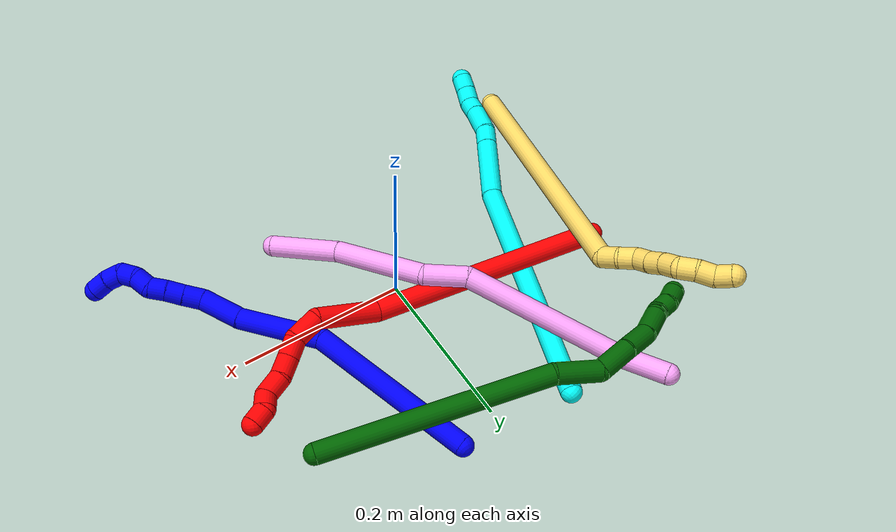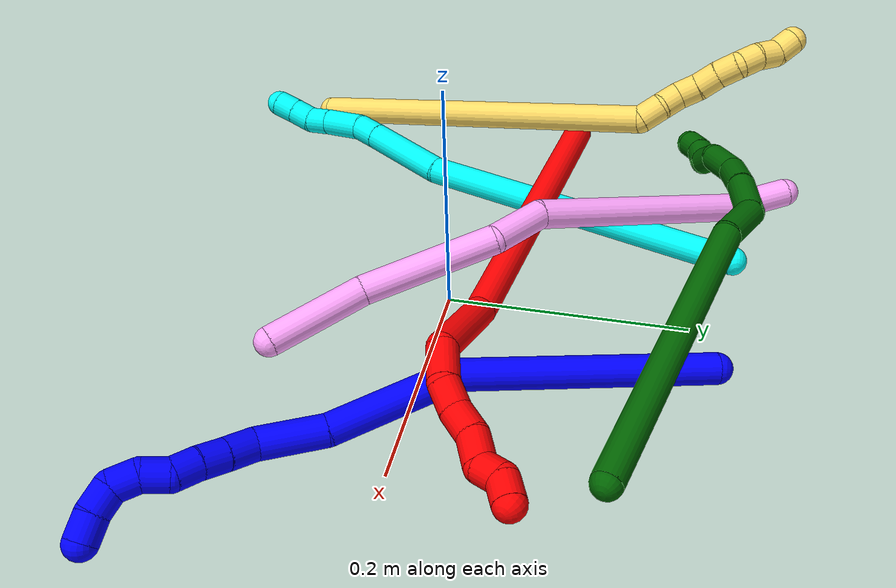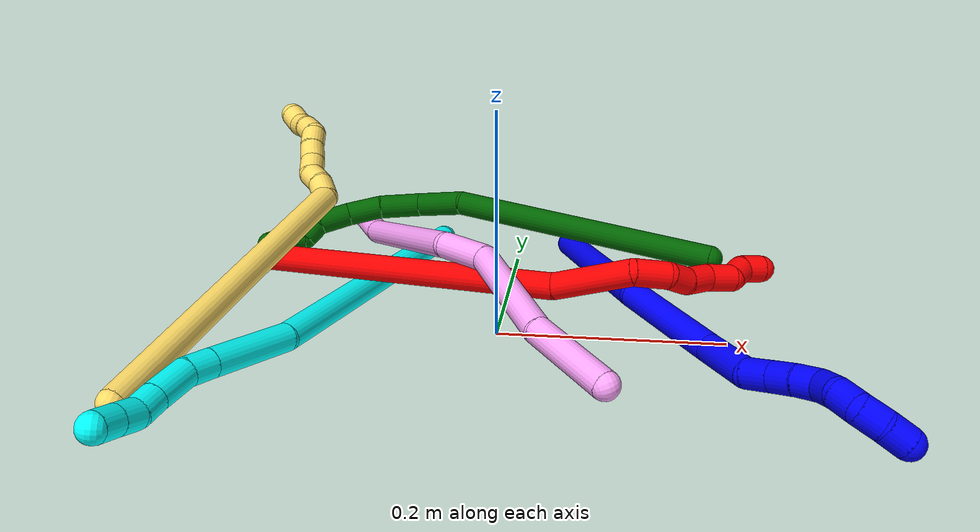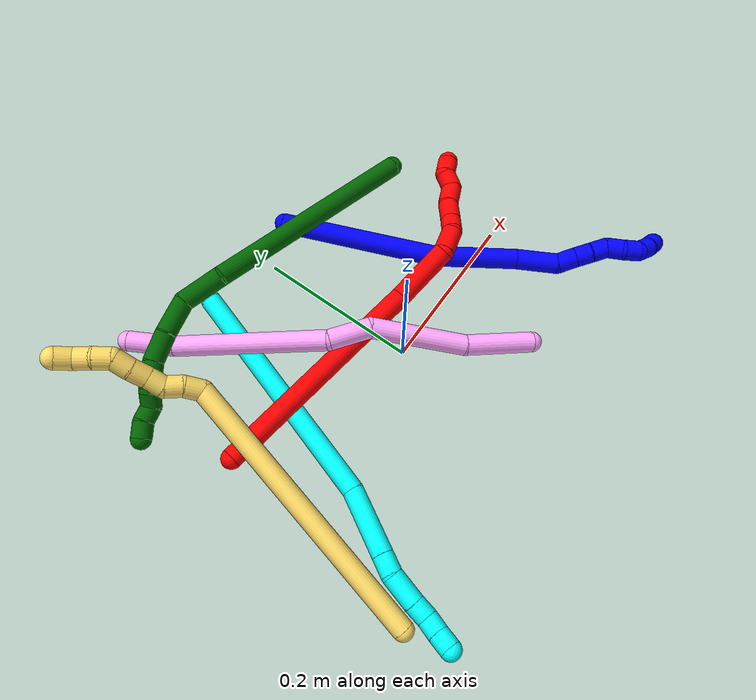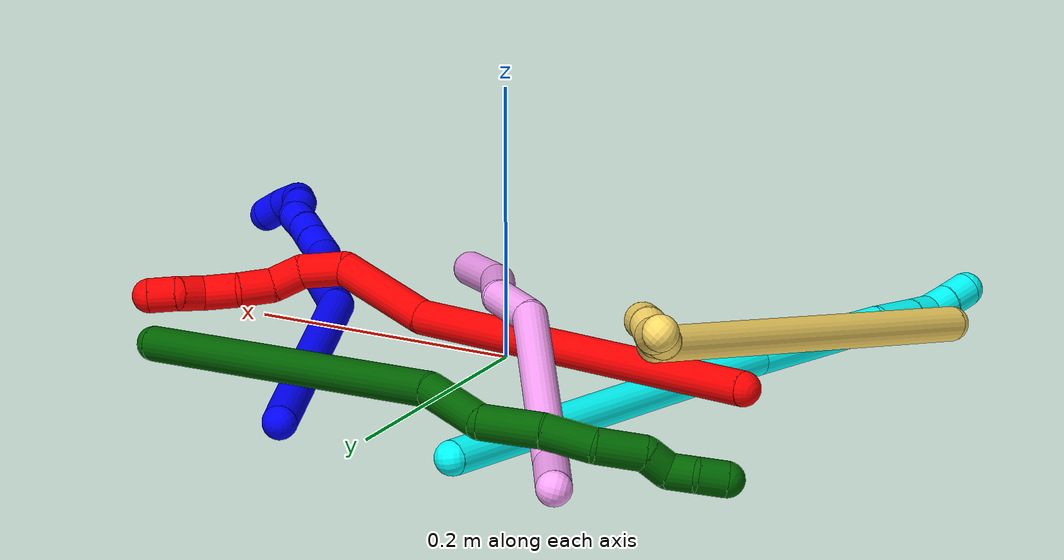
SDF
<sdf version="1.7">
 <world name="default">
  <plugin name="TubeGeneratorPlugin" filename="libtube_generator_plugin.so"/>
  <model name="photoneo_s_sensor">
   <static>1</static>
   <pose>0 0 2 1.57079 1.57079 3.14159</pose>
   <link name="link">
    <inertial><mass>0.1</mass></inertial>
    <sensor name="sensor" type="depth">
     <update_rate>30</update_rate>
     <camera>
      <horizontal_fov>1.22</horizontal_fov>
      <image><width>1920</width><height>1200</height><format>B8G8R8</format></image>
      <clip><near>0.1</near><far>4</far></clip>
      <depth_camera><output>points</output></depth_camera>
     </camera>
     <plugin name="camera_plugin" filename="libgazebo_ros_depth_camera.so">
      <baseline>0.2</baseline>
      <alwaysOn>1</alwaysOn>
      <updateRate>0.0</updateRate>
      <cameraName>camera_ir</cameraName>
      <imageTopicName>/camera/color/image_raw</imageTopicName>
      <cameraInfoTopicName>/camera/color/camera_info</cameraInfoTopicName>
      <depthImageTopicName>/camera/depth/image_raw</depthImageTopicName>
      <depthImageCameraInfoTopicName>/camera/depth/camera_info</depthImageCameraInfoTopicName>
      <pointCloudTopicName>/camera/depth/points</pointCloudTopicName>
      <frameName>fr_optical</frameName>
      <pointCloudCutoff>0.1</pointCloudCutoff>
      <pointCloudCutoffMax>2.0</pointCloudCutoffMax>
      <distortionK1>0</distortionK1>
      <distortionK2>0</distortionK2>
      <distortionK3>0</distortionK3>
      <distortionT1>0</distortionT1>
      <distortionT2>0</distortionT2>
      <CxPrime>0</CxPrime>
      <Cx>0</Cx>
      <Cy>0</Cy>
      <focalLength>0</focalLength>
      <hackBaseline>0</hackBaseline>
     </plugin>
    </sensor>
   </link>
  </model>
  <gravity>0 0 -9.8</gravity>
  <magnetic_field>6e-06 2.3e-05 -4.2e-05</magnetic_field>
  <atmosphere type="adiabatic"/>
  <physics name="default_physics" default="0" type="ode">
   <max_step_size>0.003</max_step_size>
   <real_time_factor>1</real_time_factor>
   <real_time_update_rate>1000</real_time_update_rate>
   <max_contacts>10000</max_contacts>
   <ode>
    <solver>
     <type>quick</type>
     <iters>100</iters>
     <sor>1.3</sor>
     <use_dynamic_moi_rescaling>0</use_dynamic_moi_rescaling>
    </solver>
    <constraints>
     <contact_max_correcting_vel>0</contact_max_correcting_vel>
     <contact_surface_layer>0.001</contact_surface_layer>
     <cfm>0</cfm>
     <erp>0.2</erp>
    </constraints>
   </ode>
  </physics>
  <scene><ambient>0.4 0.4 0.4 1</ambient><background>0.7 0.7 0.7 1</background><shadows>0</shadows></scene>
  <audio><device>default</device></audio>
  <spherical_coordinates>
   <surface_model>EARTH_WGS84</surface_model>
   <latitude_deg>0</latitude_deg>
   <longitude_deg>0</longitude_deg>
   <elevation>0</elevation>
   <heading_deg>0</heading_deg>
  </spherical_coordinates>
  <model name="bin">
   <static>1</static>
   <link name="bottom">
    <collision name="collision-bottom">
     <pose>0 0 -0.01 0 -0 0</pose>
     <geometry><box><size>0.8 0.6 0.02</size></box></geometry>
     <surface>
      <friction><ode><mu>100</mu><mu2>100</mu2></ode></friction>
      <contact><collide_bitmask>65535</collide_bitmask></contact>
     </surface>
    </collision>
   </link>
   <link name="west_wall">
    <collision name="collision-west_wall">
     <pose>-0.41 0 0.1 0 -0 0</pose>
     <geometry><box><size>0.02 0.6 0.2</size></box></geometry>
     <surface>
      <friction><ode><mu>100</mu><mu2>100</mu2></ode></friction>
      <contact><collide_bitmask>65535</collide_bitmask></contact>
     </surface>
    </collision>
   </link>
   <link name="east_wall">
    <collision name="collision-east_wall">
     <pose>0.41 0 0.1 0 -0 0</pose>
     <geometry><box><size>0.02 0.6 0.2</size></box></geometry>
     <surface>
      <friction><ode><mu>100</mu><mu2>100</mu2></ode></friction>
      <contact><collide_bitmask>65535</collide_bitmask></contact>
     </surface>
    </collision>
   </link>
   <link name="south_wall">
    <collision name="collision-south_wall">
     <pose>0 -0.31 0.1 0 -0 0</pose>
     <geometry><box><size>0.8 0.02 0.2</size></box></geometry>
     <surface>
      <friction><ode><mu>100</mu><mu2>100</mu2></ode></friction>
      <contact><collide_bitmask>65535</collide_bitmask></contact>
     </surface>
    </collision>
   </link>
   <link name="north_wall">
    <collision name="collision-north_wall">
     <pose>0 0.31 0.1 0 -0 0</pose>
     <geometry><box><size>0.8 0.02 0.2</size></box></geometry>
     <surface>
      <friction><ode><mu>100</mu><mu2>100</mu2></ode></friction>
      <contact><collide_bitmask>65535</collide_bitmask></contact>
     </surface>
    </collision>
   </link>
  </model>
  <model name="1">
   <static>0</static>
   <link name="1">
    <collision name="collision-cylinder-e_1_1_4">
     <pose>0.00255 -0.032547 -0.095252 2.81234 0.025325 0.152154</pose>
     <geometry><cylinder><radius>0.0125</radius><length>0.201382</length></cylinder></geometry>
     <surface>
      <friction><ode><mu>1.16</mu><mu2>1.16</mu2><slip1>0</slip1><slip2>0</slip2></ode></friction>
      <contact><ode><kp>1e+06</kp><kd>1</kd><max_vel>0</max_vel><min_depth>0.001</min_depth></ode></contact>
     </surface>
    </collision>
    <visual name="visual-cylinder-e_1_1_4">
     <pose>0.00255 -0.032547 -0.095252 2.81234 0.025325 0.152154</pose>
     <geometry><cylinder><radius>0.0125</radius><length>0.201382</length></cylinder></geometry>
     <material><ambient>0 0 1 1</ambient></material>
    </visual>
    <collision name="collision-cylinder-e_2_4_5">
     <pose>0.02279 -0.089596 -0.232172 2.61003 0.350833 1.15427</pose>
     <geometry><cylinder><radius>0.0125</radius><length>0.102947</length></cylinder></geometry>
     <surface>
      <friction><ode><mu>1.16</mu><mu2>1.16</mu2><slip1>0</slip1><slip2>0</slip2></ode></friction>
      <contact><ode><kp>1e+06</kp><kd>1</kd><max_vel>0</max_vel><min_depth>0.001</min_depth></ode></contact>
     </surface>
    </collision>
    <visual name="visual-cylinder-e_2_4_5">
     <pose>0.02279 -0.089596 -0.232172 2.61003 0.350833 1.15427</pose>
     <geometry><cylinder><radius>0.0125</radius><length>0.102947</length></cylinder></geometry>
     <material><ambient>0 0 1 1</ambient></material>
    </visual>
    <collision name="collision-cylinder-e_3_5_6">
     <pose>0.044427 -0.124945 -0.297056 2.70448 0.152816 0.663867</pose>
     <geometry><cylinder><radius>0.0125</radius><length>0.051855</length></cylinder></geometry>
     <surface>
      <friction><ode><mu>1.16</mu><mu2>1.16</mu2><slip1>0</slip1><slip2>0</slip2></ode></friction>
      <contact><ode><kp>1e+06</kp><kd>1</kd><max_vel>0</max_vel><min_depth>0.001</min_depth></ode></contact>
     </surface>
    </collision>
    <visual name="visual-cylinder-e_3_5_6">
     <pose>0.044427 -0.124945 -0.297056 2.70448 0.152816 0.663867</pose>
     <geometry><cylinder><radius>0.0125</radius><length>0.051855</length></cylinder></geometry>
     <material><ambient>0 0 1 1</ambient></material>
    </visual>
    <collision name="collision-cylinder-e_4_6_7">
     <pose>0.049779 -0.144906 -0.327656 2.25178 0.119251 0.249114</pose>
     <geometry><cylinder><radius>0.0125</radius><length>0.023626</length></cylinder></geometry>
     <surface>
      <friction><ode><mu>1.16</mu><mu2>1.16</mu2><slip1>0</slip1><slip2>0</slip2></ode></friction>
      <contact><ode><kp>1e+06</kp><kd>1</kd><max_vel>0</max_vel><min_depth>0.001</min_depth></ode></contact>
     </surface>
    </collision>
    <visual name="visual-cylinder-e_4_6_7">
     <pose>0.049779 -0.144906 -0.327656 2.25178 0.119251 0.249114</pose>
     <geometry><cylinder><radius>0.0125</radius><length>0.023626</length></cylinder></geometry>
     <material><ambient>0 0 1 1</ambient></material>
    </visual>
    <collision name="collision-cylinder-e_5_7_8">
     <pose>0.052194 -0.161553 -0.341636 2.28988 0.100455 0.220739</pose>
     <geometry><cylinder><radius>0.0125</radius><length>0.02013</length></cylinder></geometry>
     <surface>
      <friction><ode><mu>1.16</mu><mu2>1.16</mu2><slip1>0</slip1><slip2>0</slip2></ode></friction>
      <contact><ode><kp>1e+06</kp><kd>1</kd><max_vel>0</max_vel><min_depth>0.001</min_depth></ode></contact>
     </surface>
    </collision>
    <visual name="visual-cylinder-e_5_7_8">
     <pose>0.052194 -0.161553 -0.341636 2.28988 0.100455 0.220739</pose>
     <geometry><cylinder><radius>0.0125</radius><length>0.02013</length></cylinder></geometry>
     <material><ambient>0 0 1 1</ambient></material>
    </visual>
    <collision name="collision-cylinder-e_6_8_9">
     <pose>0.055243 -0.176563 -0.354563 2.27347 0.205255 0.437254</pose>
     <geometry><cylinder><radius>0.0125</radius><length>0.020011</length></cylinder></geometry>
     <surface>
      <friction><ode><mu>1.16</mu><mu2>1.16</mu2><slip1>0</slip1><slip2>0</slip2></ode></friction>
      <contact><ode><kp>1e+06</kp><kd>1</kd><max_vel>0</max_vel><min_depth>0.001</min_depth></ode></contact>
     </surface>
    </collision>
    <visual name="visual-cylinder-e_6_8_9">
     <pose>0.055243 -0.176563 -0.354563 2.27347 0.205255 0.437254</pose>
     <geometry><cylinder><radius>0.0125</radius><length>0.020011</length></cylinder></geometry>
     <material><ambient>0 0 1 1</ambient></material>
    </visual>
    <collision name="collision-cylinder-e_7_9_10">
     <pose>0.056783 -0.187899 -0.370131 2.74572 -0.04981 -0.247136</pose>
     <geometry><cylinder><radius>0.0125</radius><length>0.020048</length></cylinder></geometry>
     <surface>
      <friction><ode><mu>1.16</mu><mu2>1.16</mu2><slip1>0</slip1><slip2>0</slip2></ode></friction>
      <contact><ode><kp>1e+06</kp><kd>1</kd><max_vel>0</max_vel><min_depth>0.001</min_depth></ode></contact>
     </surface>
    </collision>
    <visual name="visual-cylinder-e_7_9_10">
     <pose>0.056783 -0.187899 -0.370131 2.74572 -0.04981 -0.247136</pose>
     <geometry><cylinder><radius>0.0125</radius><length>0.020048</length></cylinder></geometry>
     <material><ambient>0 0 1 1</ambient></material>
    </visual>
    <collision name="collision-cylinder-e_8_10_11">
     <pose>0.059705 -0.196199 -0.38765 2.64952 0.349128 1.22451</pose>
     <geometry><cylinder><radius>0.0125</radius><length>0.020001</length></cylinder></geometry>
     <surface>
      <friction><ode><mu>1.16</mu><mu2>1.16</mu2><slip1>0</slip1><slip2>0</slip2></ode></friction>
      <contact><ode><kp>1e+06</kp><kd>1</kd><max_vel>0</max_vel><min_depth>0.001</min_depth></ode></contact>
     </surface>
    </collision>
    <visual name="visual-cylinder-e_8_10_11">
     <pose>0.059705 -0.196199 -0.38765 2.64952 0.349128 1.22451</pose>
     <geometry><cylinder><radius>0.0125</radius><length>0.020001</length></cylinder></geometry>
     <material><ambient>0 0 1 1</ambient></material>
    </visual>
    <collision name="collision-cylinder-e_9_11_12">
     <pose>0.070595 -0.206243 -0.399511 2.13909 0.843381 1.37211</pose>
     <geometry><cylinder><radius>0.0125</radius><length>0.02</length></cylinder></geometry>
     <surface>
      <friction><ode><mu>1.16</mu><mu2>1.16</mu2><slip1>0</slip1><slip2>0</slip2></ode></friction>
      <contact><ode><kp>1e+06</kp><kd>1</kd><max_vel>0</max_vel><min_depth>0.001</min_depth></ode></contact>
     </surface>
    </collision>
    <visual name="visual-cylinder-e_9_11_12">
     <pose>0.070595 -0.206243 -0.399511 2.13909 0.843381 1.37211</pose>
     <geometry><cylinder><radius>0.0125</radius><length>0.02</length></cylinder></geometry>
     <material><ambient>0 0 1 1</ambient></material>
    </visual>
    <collision name="collision-cylinder-e_10_12_2">
     <pose>0.086547 -0.216879 -0.404737 1.88713 1.01285 1.3063</pose>
     <geometry><cylinder><radius>0.0125</radius><length>0.02</length></cylinder></geometry>
     <surface>
      <friction><ode><mu>1.16</mu><mu2>1.16</mu2><slip1>0</slip1><slip2>0</slip2></ode></friction>
      <contact><ode><kp>1e+06</kp><kd>1</kd><max_vel>0</max_vel><min_depth>0.001</min_depth></ode></contact>
     </surface>
    </collision>
    <visual name="visual-cylinder-e_10_12_2">
     <pose>0.086547 -0.216879 -0.404737 1.88713 1.01285 1.3063</pose>
     <geometry><cylinder><radius>0.0125</radius><length>0.02</length></cylinder></geometry>
     <material><ambient>0 0 1 1</ambient></material>
    </visual>
    <collision name="collision-sphere-2">
     <pose>0.095031 -0.221911 -0.406384 0 -0 0</pose>
     <geometry><sphere><radius>0.0125</radius></sphere></geometry>
     <surface>
      <friction><ode><mu>1.16</mu><mu2>1.16</mu2><slip1>0</slip1><slip2>0</slip2></ode></friction>
      <contact><ode><kp>1e+06</kp><kd>1</kd><max_vel>0</max_vel><min_depth>0.001</min_depth></ode></contact>
     </surface>
    </collision>
    <visual name="visual-sphere-2">
     <pose>0.095031 -0.221911 -0.406384 0 -0 0</pose>
     <geometry><sphere><radius>0.0125</radius></sphere></geometry>
     <material><ambient>0 0 1 1</ambient></material>
    </visual>
    <collision name="collision-sphere-12">
     <pose>0.078064 -0.211848 -0.40309 0 -0 0</pose>
     <geometry><sphere><radius>0.0125</radius></sphere></geometry>
     <surface>
      <friction><ode><mu>1.16</mu><mu2>1.16</mu2><slip1>0</slip1><slip2>0</slip2></ode></friction>
      <contact><ode><kp>1e+06</kp><kd>1</kd><max_vel>0</max_vel><min_depth>0.001</min_depth></ode></contact>
     </surface>
    </collision>
    <visual name="visual-sphere-12">
     <pose>0.078064 -0.211848 -0.40309 0 -0 0</pose>
     <geometry><sphere><radius>0.0125</radius></sphere></geometry>
     <material><ambient>0 0 1 1</ambient></material>
    </visual>
    <collision name="collision-sphere-11">
     <pose>0.063126 -0.200639 -0.395932 0 -0 0</pose>
     <geometry><sphere><radius>0.0125</radius></sphere></geometry>
     <surface>
      <friction><ode><mu>1.16</mu><mu2>1.16</mu2><slip1>0</slip1><slip2>0</slip2></ode></friction>
      <contact><ode><kp>1e+06</kp><kd>1</kd><max_vel>0</max_vel><min_depth>0.001</min_depth></ode></contact>
     </surface>
    </collision>
    <visual name="visual-sphere-11">
     <pose>0.063126 -0.200639 -0.395932 0 -0 0</pose>
     <geometry><sphere><radius>0.0125</radius></sphere></geometry>
     <material><ambient>0 0 1 1</ambient></material>
    </visual>
    <collision name="collision-sphere-10">
     <pose>0.056284 -0.191759 -0.379368 0 -0 0</pose>
     <geometry><sphere><radius>0.0125</radius></sphere></geometry>
     <surface>
      <friction><ode><mu>1.16</mu><mu2>1.16</mu2><slip1>0</slip1><slip2>0</slip2></ode></friction>
      <contact><ode><kp>1e+06</kp><kd>1</kd><max_vel>0</max_vel><min_depth>0.001</min_depth></ode></contact>
     </surface>
    </collision>
    <visual name="visual-sphere-10">
     <pose>0.056284 -0.191759 -0.379368 0 -0 0</pose>
     <geometry><sphere><radius>0.0125</radius></sphere></geometry>
     <material><ambient>0 0 1 1</ambient></material>
    </visual>
    <collision name="collision-sphere-9">
     <pose>0.057282 -0.184038 -0.360893 0 -0 0</pose>
     <geometry><sphere><radius>0.0125</radius></sphere></geometry>
     <surface>
      <friction><ode><mu>1.16</mu><mu2>1.16</mu2><slip1>0</slip1><slip2>0</slip2></ode></friction>
      <contact><ode><kp>1e+06</kp><kd>1</kd><max_vel>0</max_vel><min_depth>0.001</min_depth></ode></contact>
     </surface>
    </collision>
    <visual name="visual-sphere-9">
     <pose>0.057282 -0.184038 -0.360893 0 -0 0</pose>
     <geometry><sphere><radius>0.0125</radius></sphere></geometry>
     <material><ambient>0 0 1 1</ambient></material>
    </visual>
    <collision name="collision-sphere-4">
     <pose>0.0051 -0.065094 -0.190503 0 -0 0</pose>
     <geometry><sphere><radius>0.0125</radius></sphere></geometry>
     <surface>
      <friction><ode><mu>1.16</mu><mu2>1.16</mu2><slip1>0</slip1><slip2>0</slip2></ode></friction>
      <contact><ode><kp>1e+06</kp><kd>1</kd><max_vel>0</max_vel><min_depth>0.001</min_depth></ode></contact>
     </surface>
    </collision>
    <visual name="visual-sphere-4">
     <pose>0.0051 -0.065094 -0.190503 0 -0 0</pose>
     <geometry><sphere><radius>0.0125</radius></sphere></geometry>
     <material><ambient>0 0 1 1</ambient></material>
    </visual>
    <collision name="collision-sphere-1">
     <geometry><sphere><radius>0.0125</radius></sphere></geometry>
     <surface>
      <friction><ode><mu>1.16</mu><mu2>1.16</mu2><slip1>0</slip1><slip2>0</slip2></ode></friction>
      <contact><ode><kp>1e+06</kp><kd>1</kd><max_vel>0</max_vel><min_depth>0.001</min_depth></ode></contact>
     </surface>
    </collision>
    <visual name="visual-sphere-1">
     <geometry><sphere><radius>0.0125</radius></sphere></geometry>
     <material><ambient>0 0 1 1</ambient></material>
    </visual>
    <collision name="collision-sphere-8">
     <pose>0.053203 -0.169088 -0.348233 0 -0 0</pose>
     <geometry><sphere><radius>0.0125</radius></sphere></geometry>
     <surface>
      <friction><ode><mu>1.16</mu><mu2>1.16</mu2><slip1>0</slip1><slip2>0</slip2></ode></friction>
      <contact><ode><kp>1e+06</kp><kd>1</kd><max_vel>0</max_vel><min_depth>0.001</min_depth></ode></contact>
     </surface>
    </collision>
    <visual name="visual-sphere-8">
     <pose>0.053203 -0.169088 -0.348233 0 -0 0</pose>
     <geometry><sphere><radius>0.0125</radius></sphere></geometry>
     <material><ambient>0 0 1 1</ambient></material>
    </visual>
    <collision name="collision-sphere-5">
     <pose>0.04048 -0.114097 -0.27384 0 -0 0</pose>
     <geometry><sphere><radius>0.0125</radius></sphere></geometry>
     <surface>
      <friction><ode><mu>1.16</mu><mu2>1.16</mu2><slip1>0</slip1><slip2>0</slip2></ode></friction>
      <contact><ode><kp>1e+06</kp><kd>1</kd><max_vel>0</max_vel><min_depth>0.001</min_depth></ode></contact>
     </surface>
    </collision>
    <visual name="visual-sphere-5">
     <pose>0.04048 -0.114097 -0.27384 0 -0 0</pose>
     <geometry><sphere><radius>0.0125</radius></sphere></geometry>
     <material><ambient>0 0 1 1</ambient></material>
    </visual>
    <collision name="collision-sphere-6">
     <pose>0.048374 -0.135793 -0.320272 0 -0 0</pose>
     <geometry><sphere><radius>0.0125</radius></sphere></geometry>
     <surface>
      <friction><ode><mu>1.16</mu><mu2>1.16</mu2><slip1>0</slip1><slip2>0</slip2></ode></friction>
      <contact><ode><kp>1e+06</kp><kd>1</kd><max_vel>0</max_vel><min_depth>0.001</min_depth></ode></contact>
     </surface>
    </collision>
    <visual name="visual-sphere-6">
     <pose>0.048374 -0.135793 -0.320272 0 -0 0</pose>
     <geometry><sphere><radius>0.0125</radius></sphere></geometry>
     <material><ambient>0 0 1 1</ambient></material>
    </visual>
    <collision name="collision-sphere-7">
     <pose>0.051185 -0.154019 -0.33504 0 -0 0</pose>
     <geometry><sphere><radius>0.0125</radius></sphere></geometry>
     <surface>
      <friction><ode><mu>1.16</mu><mu2>1.16</mu2><slip1>0</slip1><slip2>0</slip2></ode></friction>
      <contact><ode><kp>1e+06</kp><kd>1</kd><max_vel>0</max_vel><min_depth>0.001</min_depth></ode></contact>
     </surface>
    </collision>
    <visual name="visual-sphere-7">
     <pose>0.051185 -0.154019 -0.33504 0 -0 0</pose>
     <geometry><sphere><radius>0.0125</radius></sphere></geometry>
     <material><ambient>0 0 1 1</ambient></material>
    </visual>
    <inertial>
     <pose>0.027942 -0.097239 -0.222919 0 -0 0</pose>
     <mass>0.5</mass>
     <inertia>
      <ixx>0.000939</ixx>
      <ixy>0</ixy>
      <ixz>0</ixz>
      <iyy>-0.000492</iyy>
      <iyz>0</iyz>
      <izz>0.000193</izz>
     </inertia>
    </inertial>
   </link>
   <pose>0.053963 0.224201 0.011494 -1.50724 1.11863 0.079594</pose>
  </model>
  <model name="2">
   <static>0</static>
   <link name="2">
    <collision name="collision-cylinder-e_1_1_4">
     <pose>0.023464 0.006389 -0.13638 -3.09478 0.170199 -2.60588</pose>
     <geometry><cylinder><radius>0.0125</radius><length>0.277063</length></cylinder></geometry>
     <surface>
      <friction><ode><mu>1.16</mu><mu2>1.16</mu2><slip1>0</slip1><slip2>0</slip2></ode></friction>
      <contact><ode><kp>1e+06</kp><kd>1</kd><max_vel>0</max_vel><min_depth>0.001</min_depth></ode></contact>
     </surface>
    </collision>
    <visual name="visual-cylinder-e_1_1_4">
     <pose>0.023464 0.006389 -0.13638 -3.09478 0.170199 -2.60588</pose>
     <geometry><cylinder><radius>0.0125</radius><length>0.277063</length></cylinder></geometry>
     <material><ambient>1 0 0 1</ambient></material>
    </visual>
    <collision name="collision-cylinder-e_2_4_5">
     <pose>0.052109 0.003179 -0.308704 2.88061 0.138358 0.971559</pose>
     <geometry><cylinder><radius>0.0125</radius><length>0.075125</length></cylinder></geometry>
     <surface>
      <friction><ode><mu>1.16</mu><mu2>1.16</mu2><slip1>0</slip1><slip2>0</slip2></ode></friction>
      <contact><ode><kp>1e+06</kp><kd>1</kd><max_vel>0</max_vel><min_depth>0.001</min_depth></ode></contact>
     </surface>
    </collision>
    <visual name="visual-cylinder-e_2_4_5">
     <pose>0.052109 0.003179 -0.308704 2.88061 0.138358 0.971559</pose>
     <geometry><cylinder><radius>0.0125</radius><length>0.075125</length></cylinder></geometry>
     <material><ambient>1 0 0 1</ambient></material>
    </visual>
    <collision name="collision-cylinder-e_3_5_6">
     <pose>0.065848 -0.003235 -0.358193 -2.91065 0.551441 -2.36346</pose>
     <geometry><cylinder><radius>0.0125</radius><length>0.032672</length></cylinder></geometry>
     <surface>
      <friction><ode><mu>1.16</mu><mu2>1.16</mu2><slip1>0</slip1><slip2>0</slip2></ode></friction>
      <contact><ode><kp>1e+06</kp><kd>1</kd><max_vel>0</max_vel><min_depth>0.001</min_depth></ode></contact>
     </surface>
    </collision>
    <visual name="visual-cylinder-e_3_5_6">
     <pose>0.065848 -0.003235 -0.358193 -2.91065 0.551441 -2.36346</pose>
     <geometry><cylinder><radius>0.0125</radius><length>0.032672</length></cylinder></geometry>
     <material><ambient>1 0 0 1</ambient></material>
    </visual>
    <collision name="collision-cylinder-e_4_6_7">
     <pose>0.082656 0.005299 -0.377782 -2.41711 0.796323 -1.67492</pose>
     <geometry><cylinder><radius>0.0125</radius><length>0.023082</length></cylinder></geometry>
     <surface>
      <friction><ode><mu>1.16</mu><mu2>1.16</mu2><slip1>0</slip1><slip2>0</slip2></ode></friction>
      <contact><ode><kp>1e+06</kp><kd>1</kd><max_vel>0</max_vel><min_depth>0.001</min_depth></ode></contact>
     </surface>
    </collision>
    <visual name="visual-cylinder-e_4_6_7">
     <pose>0.082656 0.005299 -0.377782 -2.41711 0.796323 -1.67492</pose>
     <geometry><cylinder><radius>0.0125</radius><length>0.023082</length></cylinder></geometry>
     <material><ambient>1 0 0 1</ambient></material>
    </visual>
    <collision name="collision-cylinder-e_5_7_8">
     <pose>0.101569 0.012362 -0.390274 -2.88175 1.01166 -2.67829</pose>
     <geometry><cylinder><radius>0.0125</radius><length>0.025157</length></cylinder></geometry>
     <surface>
      <friction><ode><mu>1.16</mu><mu2>1.16</mu2><slip1>0</slip1><slip2>0</slip2></ode></friction>
      <contact><ode><kp>1e+06</kp><kd>1</kd><max_vel>0</max_vel><min_depth>0.001</min_depth></ode></contact>
     </surface>
    </collision>
    <visual name="visual-cylinder-e_5_7_8">
     <pose>0.101569 0.012362 -0.390274 -2.88175 1.01166 -2.67829</pose>
     <geometry><cylinder><radius>0.0125</radius><length>0.025157</length></cylinder></geometry>
     <material><ambient>1 0 0 1</ambient></material>
    </visual>
    <collision name="collision-cylinder-e_6_8_9">
     <pose>0.120717 0.016392 -0.406453 -2.908 0.703536 -2.52279</pose>
     <geometry><cylinder><radius>0.0125</radius><length>0.026232</length></cylinder></geometry>
     <surface>
      <friction><ode><mu>1.16</mu><mu2>1.16</mu2><slip1>0</slip1><slip2>0</slip2></ode></friction>
      <contact><ode><kp>1e+06</kp><kd>1</kd><max_vel>0</max_vel><min_depth>0.001</min_depth></ode></contact>
     </surface>
    </collision>
    <visual name="visual-cylinder-e_6_8_9">
     <pose>0.120717 0.016392 -0.406453 -2.908 0.703536 -2.52279</pose>
     <geometry><cylinder><radius>0.0125</radius><length>0.026232</length></cylinder></geometry>
     <material><ambient>1 0 0 1</ambient></material>
    </visual>
    <collision name="collision-cylinder-e_7_9_10">
     <pose>0.138999 0.017879 -0.418572 2.80809 1.31826 2.71372</pose>
     <geometry><cylinder><radius>0.0125</radius><length>0.020236</length></cylinder></geometry>
     <surface>
      <friction><ode><mu>1.16</mu><mu2>1.16</mu2><slip1>0</slip1><slip2>0</slip2></ode></friction>
      <contact><ode><kp>1e+06</kp><kd>1</kd><max_vel>0</max_vel><min_depth>0.001</min_depth></ode></contact>
     </surface>
    </collision>
    <visual name="visual-cylinder-e_7_9_10">
     <pose>0.138999 0.017879 -0.418572 2.80809 1.31826 2.71372</pose>
     <geometry><cylinder><radius>0.0125</radius><length>0.020236</length></cylinder></geometry>
     <material><ambient>1 0 0 1</ambient></material>
    </visual>
    <collision name="collision-cylinder-e_8_10_2">
     <pose>0.155493 0.018688 -0.4285 -2.92784 0.714845 -2.58211</pose>
     <geometry><cylinder><radius>0.0125</radius><length>0.020433</length></cylinder></geometry>
     <surface>
      <friction><ode><mu>1.16</mu><mu2>1.16</mu2><slip1>0</slip1><slip2>0</slip2></ode></friction>
      <contact><ode><kp>1e+06</kp><kd>1</kd><max_vel>0</max_vel><min_depth>0.001</min_depth></ode></contact>
     </surface>
    </collision>
    <visual name="visual-cylinder-e_8_10_2">
     <pose>0.155493 0.018688 -0.4285 -2.92784 0.714845 -2.58211</pose>
     <geometry><cylinder><radius>0.0125</radius><length>0.020433</length></cylinder></geometry>
     <material><ambient>1 0 0 1</ambient></material>
    </visual>
    <collision name="collision-sphere-2">
     <pose>0.16219 0.020325 -0.43604 0 -0 0</pose>
     <geometry><sphere><radius>0.0125</radius></sphere></geometry>
     <surface>
      <friction><ode><mu>1.16</mu><mu2>1.16</mu2><slip1>0</slip1><slip2>0</slip2></ode></friction>
      <contact><ode><kp>1e+06</kp><kd>1</kd><max_vel>0</max_vel><min_depth>0.001</min_depth></ode></contact>
     </surface>
    </collision>
    <visual name="visual-sphere-2">
     <pose>0.16219 0.020325 -0.43604 0 -0 0</pose>
     <geometry><sphere><radius>0.0125</radius></sphere></geometry>
     <material><ambient>1 0 0 1</ambient></material>
    </visual>
    <collision name="collision-sphere-10">
     <pose>0.148796 0.017052 -0.420961 0 -0 0</pose>
     <geometry><sphere><radius>0.0125</radius></sphere></geometry>
     <surface>
      <friction><ode><mu>1.16</mu><mu2>1.16</mu2><slip1>0</slip1><slip2>0</slip2></ode></friction>
      <contact><ode><kp>1e+06</kp><kd>1</kd><max_vel>0</max_vel><min_depth>0.001</min_depth></ode></contact>
     </surface>
    </collision>
    <visual name="visual-sphere-10">
     <pose>0.148796 0.017052 -0.420961 0 -0 0</pose>
     <geometry><sphere><radius>0.0125</radius></sphere></geometry>
     <material><ambient>1 0 0 1</ambient></material>
    </visual>
    <collision name="collision-sphere-9">
     <pose>0.129202 0.018707 -0.416183 0 -0 0</pose>
     <geometry><sphere><radius>0.0125</radius></sphere></geometry>
     <surface>
      <friction><ode><mu>1.16</mu><mu2>1.16</mu2><slip1>0</slip1><slip2>0</slip2></ode></friction>
      <contact><ode><kp>1e+06</kp><kd>1</kd><max_vel>0</max_vel><min_depth>0.001</min_depth></ode></contact>
     </surface>
    </collision>
    <visual name="visual-sphere-9">
     <pose>0.129202 0.018707 -0.416183 0 -0 0</pose>
     <geometry><sphere><radius>0.0125</radius></sphere></geometry>
     <material><ambient>1 0 0 1</ambient></material>
    </visual>
    <collision name="collision-sphere-4">
     <pose>0.046928 0.012779 -0.27276 0 -0 0</pose>
     <geometry><sphere><radius>0.0125</radius></sphere></geometry>
     <surface>
      <friction><ode><mu>1.16</mu><mu2>1.16</mu2><slip1>0</slip1><slip2>0</slip2></ode></friction>
      <contact><ode><kp>1e+06</kp><kd>1</kd><max_vel>0</max_vel><min_depth>0.001</min_depth></ode></contact>
     </surface>
    </collision>
    <visual name="visual-sphere-4">
     <pose>0.046928 0.012779 -0.27276 0 -0 0</pose>
     <geometry><sphere><radius>0.0125</radius></sphere></geometry>
     <material><ambient>1 0 0 1</ambient></material>
    </visual>
    <collision name="collision-sphere-1">
     <geometry><sphere><radius>0.0125</radius></sphere></geometry>
     <surface>
      <friction><ode><mu>1.16</mu><mu2>1.16</mu2><slip1>0</slip1><slip2>0</slip2></ode></friction>
      <contact><ode><kp>1e+06</kp><kd>1</kd><max_vel>0</max_vel><min_depth>0.001</min_depth></ode></contact>
     </surface>
    </collision>
    <visual name="visual-sphere-1">
     <geometry><sphere><radius>0.0125</radius></sphere></geometry>
     <material><ambient>1 0 0 1</ambient></material>
    </visual>
    <collision name="collision-sphere-8">
     <pose>0.112232 0.014077 -0.396723 0 -0 0</pose>
     <geometry><sphere><radius>0.0125</radius></sphere></geometry>
     <surface>
      <friction><ode><mu>1.16</mu><mu2>1.16</mu2><slip1>0</slip1><slip2>0</slip2></ode></friction>
      <contact><ode><kp>1e+06</kp><kd>1</kd><max_vel>0</max_vel><min_depth>0.001</min_depth></ode></contact>
     </surface>
    </collision>
    <visual name="visual-sphere-8">
     <pose>0.112232 0.014077 -0.396723 0 -0 0</pose>
     <geometry><sphere><radius>0.0125</radius></sphere></geometry>
     <material><ambient>1 0 0 1</ambient></material>
    </visual>
    <collision name="collision-sphere-5">
     <pose>0.057289 -0.00642 -0.344648 0 -0 0</pose>
     <geometry><sphere><radius>0.0125</radius></sphere></geometry>
     <surface>
      <friction><ode><mu>1.16</mu><mu2>1.16</mu2><slip1>0</slip1><slip2>0</slip2></ode></friction>
      <contact><ode><kp>1e+06</kp><kd>1</kd><max_vel>0</max_vel><min_depth>0.001</min_depth></ode></contact>
     </surface>
    </collision>
    <visual name="visual-sphere-5">
     <pose>0.057289 -0.00642 -0.344648 0 -0 0</pose>
     <geometry><sphere><radius>0.0125</radius></sphere></geometry>
     <material><ambient>1 0 0 1</ambient></material>
    </visual>
    <collision name="collision-sphere-6">
     <pose>0.074407 -5e-05 -0.371738 0 -0 0</pose>
     <geometry><sphere><radius>0.0125</radius></sphere></geometry>
     <surface>
      <friction><ode><mu>1.16</mu><mu2>1.16</mu2><slip1>0</slip1><slip2>0</slip2></ode></friction>
      <contact><ode><kp>1e+06</kp><kd>1</kd><max_vel>0</max_vel><min_depth>0.001</min_depth></ode></contact>
     </surface>
    </collision>
    <visual name="visual-sphere-6">
     <pose>0.074407 -5e-05 -0.371738 0 -0 0</pose>
     <geometry><sphere><radius>0.0125</radius></sphere></geometry>
     <material><ambient>1 0 0 1</ambient></material>
    </visual>
    <collision name="collision-sphere-7">
     <pose>0.090906 0.010648 -0.383826 0 -0 0</pose>
     <geometry><sphere><radius>0.0125</radius></sphere></geometry>
     <surface>
      <friction><ode><mu>1.16</mu><mu2>1.16</mu2><slip1>0</slip1><slip2>0</slip2></ode></friction>
      <contact><ode><kp>1e+06</kp><kd>1</kd><max_vel>0</max_vel><min_depth>0.001</min_depth></ode></contact>
     </surface>
    </collision>
    <visual name="visual-sphere-7">
     <pose>0.090906 0.010648 -0.383826 0 -0 0</pose>
     <geometry><sphere><radius>0.0125</radius></sphere></geometry>
     <material><ambient>1 0 0 1</ambient></material>
    </visual>
    <inertial>
     <pose>0.052374 0.007021 -0.238212 0 -0 0</pose>
     <mass>0.5</mass>
     <inertia>
      <ixx>-0.002356</ixx>
      <ixy>0</ixy>
      <ixz>0</ixz>
      <iyy>0.000661</iyy>
      <iyz>0</iyz>
      <izz>-0.000426</izz>
     </inertia>
    </inertial>
   </link>
   <pose>-0.227019 0.07579 0.036622 -1.59407 -0.062162 1.25876</pose>
  </model>
  <model name="3">
   <static>0</static>
   <link name="3">
    <collision name="collision-cylinder-e_1_1_4">
     <pose>-0.05455 -0.108248 0.086036 0.899231 -0.375763 -0.182988</pose>
     <geometry><cylinder><radius>0.0125</radius><length>0.297291</length></cylinder></geometry>
     <surface>
      <friction><ode><mu>1.16</mu><mu2>1.16</mu2><slip1>0</slip1><slip2>0</slip2></ode></friction>
      <contact><ode><kp>1e+06</kp><kd>1</kd><max_vel>0</max_vel><min_depth>0.001</min_depth></ode></contact>
     </surface>
    </collision>
    <visual name="visual-cylinder-e_1_1_4">
     <pose>-0.05455 -0.108248 0.086036 0.899231 -0.375763 -0.182988</pose>
     <geometry><cylinder><radius>0.0125</radius><length>0.297291</length></cylinder></geometry>
     <material><ambient>0.003922 1 0.996078 1</ambient></material>
    </visual>
    <collision name="collision-cylinder-e_2_4_5">
     <pose>-0.119899 -0.240967 0.201818 0.688407 -0.273316 -0.098511</pose>
     <geometry><cylinder><radius>0.0125</radius><length>0.080008</length></cylinder></geometry>
     <surface>
      <friction><ode><mu>1.16</mu><mu2>1.16</mu2><slip1>0</slip1><slip2>0</slip2></ode></friction>
      <contact><ode><kp>1e+06</kp><kd>1</kd><max_vel>0</max_vel><min_depth>0.001</min_depth></ode></contact>
     </surface>
    </collision>
    <visual name="visual-cylinder-e_2_4_5">
     <pose>-0.119899 -0.240967 0.201818 0.688407 -0.273316 -0.098511</pose>
     <geometry><cylinder><radius>0.0125</radius><length>0.080008</length></cylinder></geometry>
     <material><ambient>0.003922 1 0.996078 1</ambient></material>
    </visual>
    <collision name="collision-cylinder-e_3_5_6">
     <pose>-0.134104 -0.272671 0.240355 0.688481 -0.290805 -0.104903</pose>
     <geometry><cylinder><radius>0.0125</radius><length>0.023763</length></cylinder></geometry>
     <surface>
      <friction><ode><mu>1.16</mu><mu2>1.16</mu2><slip1>0</slip1><slip2>0</slip2></ode></friction>
      <contact><ode><kp>1e+06</kp><kd>1</kd><max_vel>0</max_vel><min_depth>0.001</min_depth></ode></contact>
     </surface>
    </collision>
    <visual name="visual-cylinder-e_3_5_6">
     <pose>-0.134104 -0.272671 0.240355 0.688481 -0.290805 -0.104903</pose>
     <geometry><cylinder><radius>0.0125</radius><length>0.023763</length></cylinder></geometry>
     <material><ambient>0.003922 1 0.996078 1</ambient></material>
    </visual>
    <collision name="collision-cylinder-e_4_6_7">
     <pose>-0.146187 -0.293139 0.259058 0.927977 -0.483206 -0.245388</pose>
     <geometry><cylinder><radius>0.0125</radius><length>0.037349</length></cylinder></geometry>
     <surface>
      <friction><ode><mu>1.16</mu><mu2>1.16</mu2><slip1>0</slip1><slip2>0</slip2></ode></friction>
      <contact><ode><kp>1e+06</kp><kd>1</kd><max_vel>0</max_vel><min_depth>0.001</min_depth></ode></contact>
     </surface>
    </collision>
    <visual name="visual-cylinder-e_4_6_7">
     <pose>-0.146187 -0.293139 0.259058 0.927977 -0.483206 -0.245388</pose>
     <geometry><cylinder><radius>0.0125</radius><length>0.037349</length></cylinder></geometry>
     <material><ambient>0.003922 1 0.996078 1</ambient></material>
    </visual>
    <collision name="collision-cylinder-e_5_7_8">
     <pose>-0.159925 -0.314149 0.273968 0.999456 -0.501063 -0.277628</pose>
     <geometry><cylinder><radius>0.0125</radius><length>0.021073</length></cylinder></geometry>
     <surface>
      <friction><ode><mu>1.16</mu><mu2>1.16</mu2><slip1>0</slip1><slip2>0</slip2></ode></friction>
      <contact><ode><kp>1e+06</kp><kd>1</kd><max_vel>0</max_vel><min_depth>0.001</min_depth></ode></contact>
     </surface>
    </collision>
    <visual name="visual-cylinder-e_5_7_8">
     <pose>-0.159925 -0.314149 0.273968 0.999456 -0.501063 -0.277628</pose>
     <geometry><cylinder><radius>0.0125</radius><length>0.021073</length></cylinder></geometry>
     <material><ambient>0.003922 1 0.996078 1</ambient></material>
    </visual>
    <collision name="collision-cylinder-e_6_8_9">
     <pose>-0.166661 -0.329656 0.285278 0.886294 -0.166278 -0.079062</pose>
     <geometry><cylinder><radius>0.0125</radius><length>0.020246</length></cylinder></geometry>
     <surface>
      <friction><ode><mu>1.16</mu><mu2>1.16</mu2><slip1>0</slip1><slip2>0</slip2></ode></friction>
      <contact><ode><kp>1e+06</kp><kd>1</kd><max_vel>0</max_vel><min_depth>0.001</min_depth></ode></contact>
     </surface>
    </collision>
    <visual name="visual-cylinder-e_6_8_9">
     <pose>-0.166661 -0.329656 0.285278 0.886294 -0.166278 -0.079062</pose>
     <geometry><cylinder><radius>0.0125</radius><length>0.020246</length></cylinder></geometry>
     <material><ambient>0.003922 1 0.996078 1</ambient></material>
    </visual>
    <collision name="collision-cylinder-e_7_9_2">
     <pose>-0.170015 -0.345425 0.297536 0.933698 -0.166347 -0.083985</pose>
     <geometry><cylinder><radius>0.0125</radius><length>0.02027</length></cylinder></geometry>
     <surface>
      <friction><ode><mu>1.16</mu><mu2>1.16</mu2><slip1>0</slip1><slip2>0</slip2></ode></friction>
      <contact><ode><kp>1e+06</kp><kd>1</kd><max_vel>0</max_vel><min_depth>0.001</min_depth></ode></contact>
     </surface>
    </collision>
    <visual name="visual-cylinder-e_7_9_2">
     <pose>-0.170015 -0.345425 0.297536 0.933698 -0.166347 -0.083985</pose>
     <geometry><cylinder><radius>0.0125</radius><length>0.02027</length></cylinder></geometry>
     <material><ambient>0.003922 1 0.996078 1</ambient></material>
    </visual>
    <collision name="collision-sphere-2">
     <pose>-0.171693 -0.353459 0.303481 0 -0 0</pose>
     <geometry><sphere><radius>0.0125</radius></sphere></geometry>
     <surface>
      <friction><ode><mu>1.16</mu><mu2>1.16</mu2><slip1>0</slip1><slip2>0</slip2></ode></friction>
      <contact><ode><kp>1e+06</kp><kd>1</kd><max_vel>0</max_vel><min_depth>0.001</min_depth></ode></contact>
     </surface>
    </collision>
    <visual name="visual-sphere-2">
     <pose>-0.171693 -0.353459 0.303481 0 -0 0</pose>
     <geometry><sphere><radius>0.0125</radius></sphere></geometry>
     <material><ambient>0.003922 1 0.996078 1</ambient></material>
    </visual>
    <collision name="collision-sphere-9">
     <pose>-0.168337 -0.337391 0.29159 0 -0 0</pose>
     <geometry><sphere><radius>0.0125</radius></sphere></geometry>
     <surface>
      <friction><ode><mu>1.16</mu><mu2>1.16</mu2><slip1>0</slip1><slip2>0</slip2></ode></friction>
      <contact><ode><kp>1e+06</kp><kd>1</kd><max_vel>0</max_vel><min_depth>0.001</min_depth></ode></contact>
     </surface>
    </collision>
    <visual name="visual-sphere-9">
     <pose>-0.168337 -0.337391 0.29159 0 -0 0</pose>
     <geometry><sphere><radius>0.0125</radius></sphere></geometry>
     <material><ambient>0.003922 1 0.996078 1</ambient></material>
    </visual>
    <collision name="collision-sphere-4">
     <pose>-0.1091 -0.216496 0.172072 0 -0 0</pose>
     <geometry><sphere><radius>0.0125</radius></sphere></geometry>
     <surface>
      <friction><ode><mu>1.16</mu><mu2>1.16</mu2><slip1>0</slip1><slip2>0</slip2></ode></friction>
      <contact><ode><kp>1e+06</kp><kd>1</kd><max_vel>0</max_vel><min_depth>0.001</min_depth></ode></contact>
     </surface>
    </collision>
    <visual name="visual-sphere-4">
     <pose>-0.1091 -0.216496 0.172072 0 -0 0</pose>
     <geometry><sphere><radius>0.0125</radius></sphere></geometry>
     <material><ambient>0.003922 1 0.996078 1</ambient></material>
    </visual>
    <collision name="collision-sphere-1">
     <geometry><sphere><radius>0.0125</radius></sphere></geometry>
     <surface>
      <friction><ode><mu>1.16</mu><mu2>1.16</mu2><slip1>0</slip1><slip2>0</slip2></ode></friction>
      <contact><ode><kp>1e+06</kp><kd>1</kd><max_vel>0</max_vel><min_depth>0.001</min_depth></ode></contact>
     </surface>
    </collision>
    <visual name="visual-sphere-1">
     <geometry><sphere><radius>0.0125</radius></sphere></geometry>
     <material><ambient>0.003922 1 0.996078 1</ambient></material>
    </visual>
    <collision name="collision-sphere-8">
     <pose>-0.164986 -0.321922 0.278965 0 -0 0</pose>
     <geometry><sphere><radius>0.0125</radius></sphere></geometry>
     <surface>
      <friction><ode><mu>1.16</mu><mu2>1.16</mu2><slip1>0</slip1><slip2>0</slip2></ode></friction>
      <contact><ode><kp>1e+06</kp><kd>1</kd><max_vel>0</max_vel><min_depth>0.001</min_depth></ode></contact>
     </surface>
    </collision>
    <visual name="visual-sphere-8">
     <pose>-0.164986 -0.321922 0.278965 0 -0 0</pose>
     <geometry><sphere><radius>0.0125</radius></sphere></geometry>
     <material><ambient>0.003922 1 0.996078 1</ambient></material>
    </visual>
    <collision name="collision-sphere-5">
     <pose>-0.130697 -0.265439 0.231565 0 -0 0</pose>
     <geometry><sphere><radius>0.0125</radius></sphere></geometry>
     <surface>
      <friction><ode><mu>1.16</mu><mu2>1.16</mu2><slip1>0</slip1><slip2>0</slip2></ode></friction>
      <contact><ode><kp>1e+06</kp><kd>1</kd><max_vel>0</max_vel><min_depth>0.001</min_depth></ode></contact>
     </surface>
    </collision>
    <visual name="visual-sphere-5">
     <pose>-0.130697 -0.265439 0.231565 0 -0 0</pose>
     <geometry><sphere><radius>0.0125</radius></sphere></geometry>
     <material><ambient>0.003922 1 0.996078 1</ambient></material>
    </visual>
    <collision name="collision-sphere-6">
     <pose>-0.13751 -0.279903 0.249145 0 -0 0</pose>
     <geometry><sphere><radius>0.0125</radius></sphere></geometry>
     <surface>
      <friction><ode><mu>1.16</mu><mu2>1.16</mu2><slip1>0</slip1><slip2>0</slip2></ode></friction>
      <contact><ode><kp>1e+06</kp><kd>1</kd><max_vel>0</max_vel><min_depth>0.001</min_depth></ode></contact>
     </surface>
    </collision>
    <visual name="visual-sphere-6">
     <pose>-0.13751 -0.279903 0.249145 0 -0 0</pose>
     <geometry><sphere><radius>0.0125</radius></sphere></geometry>
     <material><ambient>0.003922 1 0.996078 1</ambient></material>
    </visual>
    <collision name="collision-sphere-7">
     <pose>-0.154863 -0.306375 0.268971 0 -0 0</pose>
     <geometry><sphere><radius>0.0125</radius></sphere></geometry>
     <surface>
      <friction><ode><mu>1.16</mu><mu2>1.16</mu2><slip1>0</slip1><slip2>0</slip2></ode></friction>
      <contact><ode><kp>1e+06</kp><kd>1</kd><max_vel>0</max_vel><min_depth>0.001</min_depth></ode></contact>
     </surface>
    </collision>
    <visual name="visual-sphere-7">
     <pose>-0.154863 -0.306375 0.268971 0 -0 0</pose>
     <geometry><sphere><radius>0.0125</radius></sphere></geometry>
     <material><ambient>0.003922 1 0.996078 1</ambient></material>
    </visual>
    <inertial>
     <pose>-0.089295 -0.178369 0.149384 0 -0 0</pose>
     <mass>0.5</mass>
     <inertia><ixx>0.001676</ixx><ixy>0</ixy><ixz>0</ixz><iyy>0.0011</iyy><iyz>0</iyz><izz>0.002488</izz></inertia>
    </inertial>
   </link>
   <pose>-0.085426 0.23092 0.01149 -1.15128 -1.18392 1.50266</pose>
  </model>
  <model name="4">
   <static>0</static>
   <link name="4">
    <collision name="collision-cylinder-e_1_1_4">
     <pose>0.014775 -0.023648 -0.002057 1.65754 0.556738 0.60435</pose>
     <geometry><cylinder><radius>0.0125</radius><length>0.05592</length></cylinder></geometry>
     <surface>
      <friction><ode><mu>1.16</mu><mu2>1.16</mu2><slip1>0</slip1><slip2>0</slip2></ode></friction>
      <contact><ode><kp>1e+06</kp><kd>1</kd><max_vel>0</max_vel><min_depth>0.001</min_depth></ode></contact>
     </surface>
    </collision>
    <visual name="visual-cylinder-e_1_1_4">
     <pose>0.014775 -0.023648 -0.002057 1.65754 0.556738 0.60435</pose>
     <geometry><cylinder><radius>0.0125</radius><length>0.05592</length></cylinder></geometry>
     <material><ambient>1 0.65098 0.996078 1</ambient></material>
    </visual>
    <collision name="collision-cylinder-e_2_4_5">
     <pose>0.099814 -0.111335 -0.022665 1.85277 0.811628 1.03885</pose>
     <geometry><cylinder><radius>0.0125</radius><length>0.193724</length></cylinder></geometry>
     <surface>
      <friction><ode><mu>1.16</mu><mu2>1.16</mu2><slip1>0</slip1><slip2>0</slip2></ode></friction>
      <contact><ode><kp>1e+06</kp><kd>1</kd><max_vel>0</max_vel><min_depth>0.001</min_depth></ode></contact>
     </surface>
    </collision>
    <visual name="visual-cylinder-e_2_4_5">
     <pose>0.099814 -0.111335 -0.022665 1.85277 0.811628 1.03885</pose>
     <geometry><cylinder><radius>0.0125</radius><length>0.193724</length></cylinder></geometry>
     <material><ambient>1 0.65098 0.996078 1</ambient></material>
    </visual>
    <collision name="collision-cylinder-e_3_5_6">
     <pose>0.180693 -0.195238 -0.052992 2.10592 0.430867 0.733484</pose>
     <geometry><cylinder><radius>0.0125</radius><length>0.050828</length></cylinder></geometry>
     <surface>
      <friction><ode><mu>1.16</mu><mu2>1.16</mu2><slip1>0</slip1><slip2>0</slip2></ode></friction>
      <contact><ode><kp>1e+06</kp><kd>1</kd><max_vel>0</max_vel><min_depth>0.001</min_depth></ode></contact>
     </surface>
    </collision>
    <visual name="visual-cylinder-e_3_5_6">
     <pose>0.180693 -0.195238 -0.052992 2.10592 0.430867 0.733484</pose>
     <geometry><cylinder><radius>0.0125</radius><length>0.050828</length></cylinder></geometry>
     <material><ambient>1 0.65098 0.996078 1</ambient></material>
    </visual>
    <collision name="collision-cylinder-e_4_6_7">
     <pose>0.214887 -0.267651 -0.065946 1.59321 0.421697 0.430965</pose>
     <geometry><cylinder><radius>0.0125</radius><length>0.115219</length></cylinder></geometry>
     <surface>
      <friction><ode><mu>1.16</mu><mu2>1.16</mu2><slip1>0</slip1><slip2>0</slip2></ode></friction>
      <contact><ode><kp>1e+06</kp><kd>1</kd><max_vel>0</max_vel><min_depth>0.001</min_depth></ode></contact>
     </surface>
    </collision>
    <visual name="visual-cylinder-e_4_6_7">
     <pose>0.214887 -0.267651 -0.065946 1.59321 0.421697 0.430965</pose>
     <geometry><cylinder><radius>0.0125</radius><length>0.115219</length></cylinder></geometry>
     <material><ambient>1 0.65098 0.996078 1</ambient></material>
    </visual>
    <collision name="collision-cylinder-e_5_7_2">
     <pose>0.253495 -0.358244 -0.077311 1.83243 0.364513 0.471364</pose>
     <geometry><cylinder><radius>0.0125</radius><length>0.084308</length></cylinder></geometry>
     <surface>
      <friction><ode><mu>1.16</mu><mu2>1.16</mu2><slip1>0</slip1><slip2>0</slip2></ode></friction>
      <contact><ode><kp>1e+06</kp><kd>1</kd><max_vel>0</max_vel><min_depth>0.001</min_depth></ode></contact>
     </surface>
    </collision>
    <visual name="visual-cylinder-e_5_7_2">
     <pose>0.253495 -0.358244 -0.077311 1.83243 0.364513 0.471364</pose>
     <geometry><cylinder><radius>0.0125</radius><length>0.084308</length></cylinder></geometry>
     <material><ambient>1 0.65098 0.996078 1</ambient></material>
    </visual>
    <collision name="collision-sphere-2">
     <pose>0.268523 -0.396289 -0.087498 0 -0 0</pose>
     <geometry><sphere><radius>0.0125</radius></sphere></geometry>
     <surface>
      <friction><ode><mu>1.16</mu><mu2>1.16</mu2><slip1>0</slip1><slip2>0</slip2></ode></friction>
      <contact><ode><kp>1e+06</kp><kd>1</kd><max_vel>0</max_vel><min_depth>0.001</min_depth></ode></contact>
     </surface>
    </collision>
    <visual name="visual-sphere-2">
     <pose>0.268523 -0.396289 -0.087498 0 -0 0</pose>
     <geometry><sphere><radius>0.0125</radius></sphere></geometry>
     <material><ambient>1 0.65098 0.996078 1</ambient></material>
    </visual>
    <collision name="collision-sphere-7">
     <pose>0.238468 -0.3202 -0.067123 0 -0 0</pose>
     <geometry><sphere><radius>0.0125</radius></sphere></geometry>
     <surface>
      <friction><ode><mu>1.16</mu><mu2>1.16</mu2><slip1>0</slip1><slip2>0</slip2></ode></friction>
      <contact><ode><kp>1e+06</kp><kd>1</kd><max_vel>0</max_vel><min_depth>0.001</min_depth></ode></contact>
     </surface>
    </collision>
    <visual name="visual-sphere-7">
     <pose>0.238468 -0.3202 -0.067123 0 -0 0</pose>
     <geometry><sphere><radius>0.0125</radius></sphere></geometry>
     <material><ambient>1 0.65098 0.996078 1</ambient></material>
    </visual>
    <collision name="collision-sphere-6">
     <pose>0.191307 -0.215101 -0.064768 0 -0 0</pose>
     <geometry><sphere><radius>0.0125</radius></sphere></geometry>
     <surface>
      <friction><ode><mu>1.16</mu><mu2>1.16</mu2><slip1>0</slip1><slip2>0</slip2></ode></friction>
      <contact><ode><kp>1e+06</kp><kd>1</kd><max_vel>0</max_vel><min_depth>0.001</min_depth></ode></contact>
     </surface>
    </collision>
    <visual name="visual-sphere-6">
     <pose>0.191307 -0.215101 -0.064768 0 -0 0</pose>
     <geometry><sphere><radius>0.0125</radius></sphere></geometry>
     <material><ambient>1 0.65098 0.996078 1</ambient></material>
    </visual>
    <collision name="collision-sphere-5">
     <pose>0.170078 -0.175374 -0.041217 0 -0 0</pose>
     <geometry><sphere><radius>0.0125</radius></sphere></geometry>
     <surface>
      <friction><ode><mu>1.16</mu><mu2>1.16</mu2><slip1>0</slip1><slip2>0</slip2></ode></friction>
      <contact><ode><kp>1e+06</kp><kd>1</kd><max_vel>0</max_vel><min_depth>0.001</min_depth></ode></contact>
     </surface>
    </collision>
    <visual name="visual-sphere-5">
     <pose>0.170078 -0.175374 -0.041217 0 -0 0</pose>
     <geometry><sphere><radius>0.0125</radius></sphere></geometry>
     <material><ambient>1 0.65098 0.996078 1</ambient></material>
    </visual>
    <collision name="collision-sphere-1">
     <geometry><sphere><radius>0.0125</radius></sphere></geometry>
     <surface>
      <friction><ode><mu>1.16</mu><mu2>1.16</mu2><slip1>0</slip1><slip2>0</slip2></ode></friction>
      <contact><ode><kp>1e+06</kp><kd>1</kd><max_vel>0</max_vel><min_depth>0.001</min_depth></ode></contact>
     </surface>
    </collision>
    <visual name="visual-sphere-1">
     <geometry><sphere><radius>0.0125</radius></sphere></geometry>
     <material><ambient>1 0.65098 0.996078 1</ambient></material>
    </visual>
    <collision name="collision-sphere-4">
     <pose>0.029549 -0.047296 -0.004113 0 -0 0</pose>
     <geometry><sphere><radius>0.0125</radius></sphere></geometry>
     <surface>
      <friction><ode><mu>1.16</mu><mu2>1.16</mu2><slip1>0</slip1><slip2>0</slip2></ode></friction>
      <contact><ode><kp>1e+06</kp><kd>1</kd><max_vel>0</max_vel><min_depth>0.001</min_depth></ode></contact>
     </surface>
    </collision>
    <visual name="visual-sphere-4">
     <pose>0.029549 -0.047296 -0.004113 0 -0 0</pose>
     <geometry><sphere><radius>0.0125</radius></sphere></geometry>
     <material><ambient>1 0.65098 0.996078 1</ambient></material>
    </visual>
    <inertial>
     <pose>0.150956 -0.187712 -0.042631 0 -0 0</pose>
     <mass>0.5</mass>
     <inertia>
      <ixx>0.000862</ixx>
      <ixy>0</ixy>
      <ixz>0</ixz>
      <iyy>0.000721</iyy>
      <iyz>0</iyz>
      <izz>5.9e-05</izz>
     </inertia>
    </inertial>
   </link>
   <pose>-0.186484 0.273642 0.021065 1.99885 -0.867441 -1.47538</pose>
  </model>
  <model name="5">
   <static>0</static>
   <link name="5">
    <collision name="collision-cylinder-e_1_1_4">
     <pose>-0.040681 0.149305 -0.066925 -1.99219 -0.243692 0.373749</pose>
     <geometry><cylinder><radius>0.0125</radius><length>0.337199</length></cylinder></geometry>
     <surface>
      <friction><ode><mu>1.16</mu><mu2>1.16</mu2><slip1>0</slip1><slip2>0</slip2></ode></friction>
      <contact><ode><kp>1e+06</kp><kd>1</kd><max_vel>0</max_vel><min_depth>0.001</min_depth></ode></contact>
     </surface>
    </collision>
    <visual name="visual-cylinder-e_1_1_4">
     <pose>-0.040681 0.149305 -0.066925 -1.99219 -0.243692 0.373749</pose>
     <geometry><cylinder><radius>0.0125</radius><length>0.337199</length></cylinder></geometry>
     <material><ambient>1 0.858824 0.4 1</ambient></material>
    </visual>
    <collision name="collision-cylinder-e_2_4_5">
     <pose>-0.088154 0.30692 -0.131492 -1.29418 -0.666249 0.511471</pose>
     <geometry><cylinder><radius>0.0125</radius><length>0.021979</length></cylinder></geometry>
     <surface>
      <friction><ode><mu>1.16</mu><mu2>1.16</mu2><slip1>0</slip1><slip2>0</slip2></ode></friction>
      <contact><ode><kp>1e+06</kp><kd>1</kd><max_vel>0</max_vel><min_depth>0.001</min_depth></ode></contact>
     </surface>
    </collision>
    <visual name="visual-cylinder-e_2_4_5">
     <pose>-0.088154 0.30692 -0.131492 -1.29418 -0.666249 0.511471</pose>
     <geometry><cylinder><radius>0.0125</radius><length>0.021979</length></cylinder></geometry>
     <material><ambient>1 0.858824 0.4 1</ambient></material>
    </visual>
    <collision name="collision-cylinder-e_3_5_6">
     <pose>-0.103217 0.320547 -0.126935 -1.17881 -0.963137 0.672393</pose>
     <geometry><cylinder><radius>0.0125</radius><length>0.020151</length></cylinder></geometry>
     <surface>
      <friction><ode><mu>1.16</mu><mu2>1.16</mu2><slip1>0</slip1><slip2>0</slip2></ode></friction>
      <contact><ode><kp>1e+06</kp><kd>1</kd><max_vel>0</max_vel><min_depth>0.001</min_depth></ode></contact>
     </surface>
    </collision>
    <visual name="visual-cylinder-e_3_5_6">
     <pose>-0.103217 0.320547 -0.126935 -1.17881 -0.963137 0.672393</pose>
     <geometry><cylinder><radius>0.0125</radius><length>0.020151</length></cylinder></geometry>
     <material><ambient>1 0.858824 0.4 1</ambient></material>
    </visual>
    <collision name="collision-cylinder-e_4_6_7">
     <pose>-0.115722 0.33495 -0.124365 -1.52991 -0.435613 0.418671</pose>
     <geometry><cylinder><radius>0.0125</radius><length>0.020062</length></cylinder></geometry>
     <surface>
      <friction><ode><mu>1.16</mu><mu2>1.16</mu2><slip1>0</slip1><slip2>0</slip2></ode></friction>
      <contact><ode><kp>1e+06</kp><kd>1</kd><max_vel>0</max_vel><min_depth>0.001</min_depth></ode></contact>
     </surface>
    </collision>
    <visual name="visual-cylinder-e_4_6_7">
     <pose>-0.115722 0.33495 -0.124365 -1.52991 -0.435613 0.418671</pose>
     <geometry><cylinder><radius>0.0125</radius><length>0.020062</length></cylinder></geometry>
     <material><ambient>1 0.858824 0.4 1</ambient></material>
    </visual>
    <collision name="collision-cylinder-e_5_7_8">
     <pose>-0.124198 0.352987 -0.122167 -1.36954 -0.434827 0.356936</pose>
     <geometry><cylinder><radius>0.0125</radius><length>0.020145</length></cylinder></geometry>
     <surface>
      <friction><ode><mu>1.16</mu><mu2>1.16</mu2><slip1>0</slip1><slip2>0</slip2></ode></friction>
      <contact><ode><kp>1e+06</kp><kd>1</kd><max_vel>0</max_vel><min_depth>0.001</min_depth></ode></contact>
     </surface>
    </collision>
    <visual name="visual-cylinder-e_5_7_8">
     <pose>-0.124198 0.352987 -0.122167 -1.36954 -0.434827 0.356936</pose>
     <geometry><cylinder><radius>0.0125</radius><length>0.020145</length></cylinder></geometry>
     <material><ambient>1 0.858824 0.4 1</ambient></material>
    </visual>
    <collision name="collision-cylinder-e_6_8_9">
     <pose>-0.132331 0.371328 -0.119813 -1.51462 -0.392253 0.371316</pose>
     <geometry><cylinder><radius>0.0125</radius><length>0.020356</length></cylinder></geometry>
     <surface>
      <friction><ode><mu>1.16</mu><mu2>1.16</mu2><slip1>0</slip1><slip2>0</slip2></ode></friction>
      <contact><ode><kp>1e+06</kp><kd>1</kd><max_vel>0</max_vel><min_depth>0.001</min_depth></ode></contact>
     </surface>
    </collision>
    <visual name="visual-cylinder-e_6_8_9">
     <pose>-0.132331 0.371328 -0.119813 -1.51462 -0.392253 0.371316</pose>
     <geometry><cylinder><radius>0.0125</radius><length>0.020356</length></cylinder></geometry>
     <material><ambient>1 0.858824 0.4 1</ambient></material>
    </visual>
    <collision name="collision-cylinder-e_7_9_10">
     <pose>-0.144572 0.386134 -0.118232 -1.37877 -0.98689 0.83458</pose>
     <geometry><cylinder><radius>0.0125</radius><length>0.020017</length></cylinder></geometry>
     <surface>
      <friction><ode><mu>1.16</mu><mu2>1.16</mu2><slip1>0</slip1><slip2>0</slip2></ode></friction>
      <contact><ode><kp>1e+06</kp><kd>1</kd><max_vel>0</max_vel><min_depth>0.001</min_depth></ode></contact>
     </surface>
    </collision>
    <visual name="visual-cylinder-e_7_9_10">
     <pose>-0.144572 0.386134 -0.118232 -1.37877 -0.98689 0.83458</pose>
     <geometry><cylinder><radius>0.0125</radius><length>0.020017</length></cylinder></geometry>
     <material><ambient>1 0.858824 0.4 1</ambient></material>
    </visual>
    <collision name="collision-cylinder-e_8_10_11">
     <pose>-0.161936 0.395856 -0.118008 -1.76101 -1.11801 1.29657</pose>
     <geometry><cylinder><radius>0.0125</radius><length>0.020046</length></cylinder></geometry>
     <surface>
      <friction><ode><mu>1.16</mu><mu2>1.16</mu2><slip1>0</slip1><slip2>0</slip2></ode></friction>
      <contact><ode><kp>1e+06</kp><kd>1</kd><max_vel>0</max_vel><min_depth>0.001</min_depth></ode></contact>
     </surface>
    </collision>
    <visual name="visual-cylinder-e_8_10_11">
     <pose>-0.161936 0.395856 -0.118008 -1.76101 -1.11801 1.29657</pose>
     <geometry><cylinder><radius>0.0125</radius><length>0.020046</length></cylinder></geometry>
     <material><ambient>1 0.858824 0.4 1</ambient></material>
    </visual>
    <collision name="collision-cylinder-e_9_11_2">
     <pose>-0.178348 0.406198 -0.115794 -1.10381 -0.830548 0.530189</pose>
     <geometry><cylinder><radius>0.0125</radius><length>0.020046</length></cylinder></geometry>
     <surface>
      <friction><ode><mu>1.16</mu><mu2>1.16</mu2><slip1>0</slip1><slip2>0</slip2></ode></friction>
      <contact><ode><kp>1e+06</kp><kd>1</kd><max_vel>0</max_vel><min_depth>0.001</min_depth></ode></contact>
     </surface>
    </collision>
    <visual name="visual-cylinder-e_9_11_2">
     <pose>-0.178348 0.406198 -0.115794 -1.10381 -0.830548 0.530189</pose>
     <geometry><cylinder><radius>0.0125</radius><length>0.020046</length></cylinder></geometry>
     <material><ambient>1 0.858824 0.4 1</ambient></material>
    </visual>
    <collision name="collision-sphere-2">
     <pose>-0.185748 0.412234 -0.11275 0 -0 0</pose>
     <geometry><sphere><radius>0.0125</radius></sphere></geometry>
     <surface>
      <friction><ode><mu>1.16</mu><mu2>1.16</mu2><slip1>0</slip1><slip2>0</slip2></ode></friction>
      <contact><ode><kp>1e+06</kp><kd>1</kd><max_vel>0</max_vel><min_depth>0.001</min_depth></ode></contact>
     </surface>
    </collision>
    <visual name="visual-sphere-2">
     <pose>-0.185748 0.412234 -0.11275 0 -0 0</pose>
     <geometry><sphere><radius>0.0125</radius></sphere></geometry>
     <material><ambient>1 0.858824 0.4 1</ambient></material>
    </visual>
    <collision name="collision-sphere-11">
     <pose>-0.170949 0.400161 -0.118837 0 -0 0</pose>
     <geometry><sphere><radius>0.0125</radius></sphere></geometry>
     <surface>
      <friction><ode><mu>1.16</mu><mu2>1.16</mu2><slip1>0</slip1><slip2>0</slip2></ode></friction>
      <contact><ode><kp>1e+06</kp><kd>1</kd><max_vel>0</max_vel><min_depth>0.001</min_depth></ode></contact>
     </surface>
    </collision>
    <visual name="visual-sphere-11">
     <pose>-0.170949 0.400161 -0.118837 0 -0 0</pose>
     <geometry><sphere><radius>0.0125</radius></sphere></geometry>
     <material><ambient>1 0.858824 0.4 1</ambient></material>
    </visual>
    <collision name="collision-sphere-10">
     <pose>-0.152923 0.39155 -0.117179 0 -0 0</pose>
     <geometry><sphere><radius>0.0125</radius></sphere></geometry>
     <surface>
      <friction><ode><mu>1.16</mu><mu2>1.16</mu2><slip1>0</slip1><slip2>0</slip2></ode></friction>
      <contact><ode><kp>1e+06</kp><kd>1</kd><max_vel>0</max_vel><min_depth>0.001</min_depth></ode></contact>
     </surface>
    </collision>
    <visual name="visual-sphere-10">
     <pose>-0.152923 0.39155 -0.117179 0 -0 0</pose>
     <geometry><sphere><radius>0.0125</radius></sphere></geometry>
     <material><ambient>1 0.858824 0.4 1</ambient></material>
    </visual>
    <collision name="collision-sphere-9">
     <pose>-0.136222 0.380718 -0.119285 0 -0 0</pose>
     <geometry><sphere><radius>0.0125</radius></sphere></geometry>
     <surface>
      <friction><ode><mu>1.16</mu><mu2>1.16</mu2><slip1>0</slip1><slip2>0</slip2></ode></friction>
      <contact><ode><kp>1e+06</kp><kd>1</kd><max_vel>0</max_vel><min_depth>0.001</min_depth></ode></contact>
     </surface>
    </collision>
    <visual name="visual-sphere-9">
     <pose>-0.136222 0.380718 -0.119285 0 -0 0</pose>
     <geometry><sphere><radius>0.0125</radius></sphere></geometry>
     <material><ambient>1 0.858824 0.4 1</ambient></material>
    </visual>
    <collision name="collision-sphere-4">
     <pose>-0.081362 0.298609 -0.133851 0 -0 0</pose>
     <geometry><sphere><radius>0.0125</radius></sphere></geometry>
     <surface>
      <friction><ode><mu>1.16</mu><mu2>1.16</mu2><slip1>0</slip1><slip2>0</slip2></ode></friction>
      <contact><ode><kp>1e+06</kp><kd>1</kd><max_vel>0</max_vel><min_depth>0.001</min_depth></ode></contact>
     </surface>
    </collision>
    <visual name="visual-sphere-4">
     <pose>-0.081362 0.298609 -0.133851 0 -0 0</pose>
     <geometry><sphere><radius>0.0125</radius></sphere></geometry>
     <material><ambient>1 0.858824 0.4 1</ambient></material>
    </visual>
    <collision name="collision-sphere-1">
     <geometry><sphere><radius>0.0125</radius></sphere></geometry>
     <surface>
      <friction><ode><mu>1.16</mu><mu2>1.16</mu2><slip1>0</slip1><slip2>0</slip2></ode></friction>
      <contact><ode><kp>1e+06</kp><kd>1</kd><max_vel>0</max_vel><min_depth>0.001</min_depth></ode></contact>
     </surface>
    </collision>
    <visual name="visual-sphere-1">
     <geometry><sphere><radius>0.0125</radius></sphere></geometry>
     <material><ambient>1 0.858824 0.4 1</ambient></material>
    </visual>
    <collision name="collision-sphere-8">
     <pose>-0.128441 0.361937 -0.120341 0 -0 0</pose>
     <geometry><sphere><radius>0.0125</radius></sphere></geometry>
     <surface>
      <friction><ode><mu>1.16</mu><mu2>1.16</mu2><slip1>0</slip1><slip2>0</slip2></ode></friction>
      <contact><ode><kp>1e+06</kp><kd>1</kd><max_vel>0</max_vel><min_depth>0.001</min_depth></ode></contact>
     </surface>
    </collision>
    <visual name="visual-sphere-8">
     <pose>-0.128441 0.361937 -0.120341 0 -0 0</pose>
     <geometry><sphere><radius>0.0125</radius></sphere></geometry>
     <material><ambient>1 0.858824 0.4 1</ambient></material>
    </visual>
    <collision name="collision-sphere-5">
     <pose>-0.094945 0.315231 -0.129132 0 -0 0</pose>
     <geometry><sphere><radius>0.0125</radius></sphere></geometry>
     <surface>
      <friction><ode><mu>1.16</mu><mu2>1.16</mu2><slip1>0</slip1><slip2>0</slip2></ode></friction>
      <contact><ode><kp>1e+06</kp><kd>1</kd><max_vel>0</max_vel><min_depth>0.001</min_depth></ode></contact>
     </surface>
    </collision>
    <visual name="visual-sphere-5">
     <pose>-0.094945 0.315231 -0.129132 0 -0 0</pose>
     <geometry><sphere><radius>0.0125</radius></sphere></geometry>
     <material><ambient>1 0.858824 0.4 1</ambient></material>
    </visual>
    <collision name="collision-sphere-6">
     <pose>-0.111489 0.325863 -0.124737 0 -0 0</pose>
     <geometry><sphere><radius>0.0125</radius></sphere></geometry>
     <surface>
      <friction><ode><mu>1.16</mu><mu2>1.16</mu2><slip1>0</slip1><slip2>0</slip2></ode></friction>
      <contact><ode><kp>1e+06</kp><kd>1</kd><max_vel>0</max_vel><min_depth>0.001</min_depth></ode></contact>
     </surface>
    </collision>
    <visual name="visual-sphere-6">
     <pose>-0.111489 0.325863 -0.124737 0 -0 0</pose>
     <geometry><sphere><radius>0.0125</radius></sphere></geometry>
     <material><ambient>1 0.858824 0.4 1</ambient></material>
    </visual>
    <collision name="collision-sphere-7">
     <pose>-0.119954 0.344036 -0.123993 0 -0 0</pose>
     <geometry><sphere><radius>0.0125</radius></sphere></geometry>
     <surface>
      <friction><ode><mu>1.16</mu><mu2>1.16</mu2><slip1>0</slip1><slip2>0</slip2></ode></friction>
      <contact><ode><kp>1e+06</kp><kd>1</kd><max_vel>0</max_vel><min_depth>0.001</min_depth></ode></contact>
     </surface>
    </collision>
    <visual name="visual-sphere-7">
     <pose>-0.119954 0.344036 -0.123993 0 -0 0</pose>
     <geometry><sphere><radius>0.0125</radius></sphere></geometry>
     <material><ambient>1 0.858824 0.4 1</ambient></material>
    </visual>
    <inertial>
     <pose>-0.069935 0.217494 -0.084927 0 -0 0</pose>
     <mass>0.5</mass>
     <inertia>
      <ixx>0.004032</ixx>
      <ixy>0</ixy>
      <ixz>0</ixz>
      <iyy>0.000216</iyy>
      <iyz>0</iyz>
      <izz>-0.002076</izz>
     </inertia>
    </inertial>
   </link>
   <pose>-0.263712 -0.185222 0.012163 0.718318 -0.288761 -0.550227</pose>
  </model>
  <model name="6">
   <static>0</static>
   <link name="6">
    <collision name="collision-cylinder-e_1_1_4">
     <pose>-0.013049 0.010372 -0.134602 -3.06469 -0.096362 1.79475</pose>
     <geometry><cylinder><radius>0.0125</radius><length>0.27126</length></cylinder></geometry>
     <surface>
      <friction><ode><mu>1.16</mu><mu2>1.16</mu2><slip1>0</slip1><slip2>0</slip2></ode></friction>
      <contact><ode><kp>1e+06</kp><kd>1</kd><max_vel>0</max_vel><min_depth>0.001</min_depth></ode></contact>
     </surface>
    </collision>
    <visual name="visual-cylinder-e_1_1_4">
     <pose>-0.013049 0.010372 -0.134602 -3.06469 -0.096362 1.79475</pose>
     <geometry><cylinder><radius>0.0125</radius><length>0.27126</length></cylinder></geometry>
     <material><ambient>0 0.392157 0.003922 1</ambient></material>
    </visual>
    <collision name="collision-cylinder-e_2_4_5">
     <pose>-0.020821 0.021062 -0.295269 -3.12936 0.199774 -3.01969</pose>
     <geometry><cylinder><radius>0.0125</radius><length>0.053193</length></cylinder></geometry>
     <surface>
      <friction><ode><mu>1.16</mu><mu2>1.16</mu2><slip1>0</slip1><slip2>0</slip2></ode></friction>
      <contact><ode><kp>1e+06</kp><kd>1</kd><max_vel>0</max_vel><min_depth>0.001</min_depth></ode></contact>
     </surface>
    </collision>
    <visual name="visual-cylinder-e_2_4_5">
     <pose>-0.020821 0.021062 -0.295269 -3.12936 0.199774 -3.01969</pose>
     <geometry><cylinder><radius>0.0125</radius><length>0.053193</length></cylinder></geometry>
     <material><ambient>0 0.392157 0.003922 1</ambient></material>
    </visual>
    <collision name="collision-cylinder-e_3_5_6">
     <pose>-0.02052 0.013385 -0.341315 2.76091 -0.22728 -1.06956</pose>
     <geometry><cylinder><radius>0.0125</radius><length>0.04418</length></cylinder></geometry>
     <surface>
      <friction><ode><mu>1.16</mu><mu2>1.16</mu2><slip1>0</slip1><slip2>0</slip2></ode></friction>
      <contact><ode><kp>1e+06</kp><kd>1</kd><max_vel>0</max_vel><min_depth>0.001</min_depth></ode></contact>
     </surface>
    </collision>
    <visual name="visual-cylinder-e_3_5_6">
     <pose>-0.02052 0.013385 -0.341315 2.76091 -0.22728 -1.06956</pose>
     <geometry><cylinder><radius>0.0125</radius><length>0.04418</length></cylinder></geometry>
     <material><ambient>0 0.392157 0.003922 1</ambient></material>
    </visual>
    <collision name="collision-cylinder-e_4_6_7">
     <pose>-0.027536 -0.003227 -0.377143 2.64361 -0.112513 -0.435931</pose>
     <geometry><cylinder><radius>0.0125</radius><length>0.036305</length></cylinder></geometry>
     <surface>
      <friction><ode><mu>1.16</mu><mu2>1.16</mu2><slip1>0</slip1><slip2>0</slip2></ode></friction>
      <contact><ode><kp>1e+06</kp><kd>1</kd><max_vel>0</max_vel><min_depth>0.001</min_depth></ode></contact>
     </surface>
    </collision>
    <visual name="visual-cylinder-e_4_6_7">
     <pose>-0.027536 -0.003227 -0.377143 2.64361 -0.112513 -0.435931</pose>
     <geometry><cylinder><radius>0.0125</radius><length>0.036305</length></cylinder></geometry>
     <material><ambient>0 0.392157 0.003922 1</ambient></material>
    </visual>
    <collision name="collision-cylinder-e_5_7_8">
     <pose>-0.034146 -0.023285 -0.405035 2.38184 -0.268536 -0.652466</pose>
     <geometry><cylinder><radius>0.0125</radius><length>0.034461</length></cylinder></geometry>
     <surface>
      <friction><ode><mu>1.16</mu><mu2>1.16</mu2><slip1>0</slip1><slip2>0</slip2></ode></friction>
      <contact><ode><kp>1e+06</kp><kd>1</kd><max_vel>0</max_vel><min_depth>0.001</min_depth></ode></contact>
     </surface>
    </collision>
    <visual name="visual-cylinder-e_5_7_8">
     <pose>-0.034146 -0.023285 -0.405035 2.38184 -0.268536 -0.652466</pose>
     <geometry><cylinder><radius>0.0125</radius><length>0.034461</length></cylinder></geometry>
     <material><ambient>0 0.392157 0.003922 1</ambient></material>
    </visual>
    <collision name="collision-cylinder-e_6_8_9">
     <pose>-0.036794 -0.04325 -0.422125 2.10531 0.191757 0.334248</pose>
     <geometry><cylinder><radius>0.0125</radius><length>0.020178</length></cylinder></geometry>
     <surface>
      <friction><ode><mu>1.16</mu><mu2>1.16</mu2><slip1>0</slip1><slip2>0</slip2></ode></friction>
      <contact><ode><kp>1e+06</kp><kd>1</kd><max_vel>0</max_vel><min_depth>0.001</min_depth></ode></contact>
     </surface>
    </collision>
    <visual name="visual-cylinder-e_6_8_9">
     <pose>-0.036794 -0.04325 -0.422125 2.10531 0.191757 0.334248</pose>
     <geometry><cylinder><radius>0.0125</radius><length>0.020178</length></cylinder></geometry>
     <material><ambient>0 0.392157 0.003922 1</ambient></material>
    </visual>
    <collision name="collision-cylinder-e_7_9_10">
     <pose>-0.037168 -0.055531 -0.436163 2.74567 -0.231445 -1.05043</pose>
     <geometry><cylinder><radius>0.0125</radius><length>0.020027</length></cylinder></geometry>
     <surface>
      <friction><ode><mu>1.16</mu><mu2>1.16</mu2><slip1>0</slip1><slip2>0</slip2></ode></friction>
      <contact><ode><kp>1e+06</kp><kd>1</kd><max_vel>0</max_vel><min_depth>0.001</min_depth></ode></contact>
     </surface>
    </collision>
    <visual name="visual-cylinder-e_7_9_10">
     <pose>-0.037168 -0.055531 -0.436163 2.74567 -0.231445 -1.05043</pose>
     <geometry><cylinder><radius>0.0125</radius><length>0.020027</length></cylinder></geometry>
     <material><ambient>0 0.392157 0.003922 1</ambient></material>
    </visual>
    <collision name="collision-cylinder-e_8_10_2">
     <pose>-0.042282 -0.06607 -0.452234 2.37776 -0.279838 -0.674532</pose>
     <geometry><cylinder><radius>0.0125</radius><length>0.020397</length></cylinder></geometry>
     <surface>
      <friction><ode><mu>1.16</mu><mu2>1.16</mu2><slip1>0</slip1><slip2>0</slip2></ode></friction>
      <contact><ode><kp>1e+06</kp><kd>1</kd><max_vel>0</max_vel><min_depth>0.001</min_depth></ode></contact>
     </surface>
    </collision>
    <visual name="visual-cylinder-e_8_10_2">
     <pose>-0.042282 -0.06607 -0.452234 2.37776 -0.279838 -0.674532</pose>
     <geometry><cylinder><radius>0.0125</radius><length>0.020397</length></cylinder></geometry>
     <material><ambient>0 0.392157 0.003922 1</ambient></material>
    </visual>
    <collision name="collision-sphere-2">
     <pose>-0.045099 -0.07285 -0.459313 0 -0 0</pose>
     <geometry><sphere><radius>0.0125</radius></sphere></geometry>
     <surface>
      <friction><ode><mu>1.16</mu><mu2>1.16</mu2><slip1>0</slip1><slip2>0</slip2></ode></friction>
      <contact><ode><kp>1e+06</kp><kd>1</kd><max_vel>0</max_vel><min_depth>0.001</min_depth></ode></contact>
     </surface>
    </collision>
    <visual name="visual-sphere-2">
     <pose>-0.045099 -0.07285 -0.459313 0 -0 0</pose>
     <geometry><sphere><radius>0.0125</radius></sphere></geometry>
     <material><ambient>0 0.392157 0.003922 1</ambient></material>
    </visual>
    <collision name="collision-sphere-10">
     <pose>-0.039465 -0.05929 -0.445155 0 -0 0</pose>
     <geometry><sphere><radius>0.0125</radius></sphere></geometry>
     <surface>
      <friction><ode><mu>1.16</mu><mu2>1.16</mu2><slip1>0</slip1><slip2>0</slip2></ode></friction>
      <contact><ode><kp>1e+06</kp><kd>1</kd><max_vel>0</max_vel><min_depth>0.001</min_depth></ode></contact>
     </surface>
    </collision>
    <visual name="visual-sphere-10">
     <pose>-0.039465 -0.05929 -0.445155 0 -0 0</pose>
     <geometry><sphere><radius>0.0125</radius></sphere></geometry>
     <material><ambient>0 0.392157 0.003922 1</ambient></material>
    </visual>
    <collision name="collision-sphere-9">
     <pose>-0.034872 -0.051772 -0.42717 0 -0 0</pose>
     <geometry><sphere><radius>0.0125</radius></sphere></geometry>
     <surface>
      <friction><ode><mu>1.16</mu><mu2>1.16</mu2><slip1>0</slip1><slip2>0</slip2></ode></friction>
      <contact><ode><kp>1e+06</kp><kd>1</kd><max_vel>0</max_vel><min_depth>0.001</min_depth></ode></contact>
     </surface>
    </collision>
    <visual name="visual-sphere-9">
     <pose>-0.034872 -0.051772 -0.42717 0 -0 0</pose>
     <geometry><sphere><radius>0.0125</radius></sphere></geometry>
     <material><ambient>0 0.392157 0.003922 1</ambient></material>
    </visual>
    <collision name="collision-sphere-4">
     <pose>-0.026099 0.020744 -0.269204 0 -0 0</pose>
     <geometry><sphere><radius>0.0125</radius></sphere></geometry>
     <surface>
      <friction><ode><mu>1.16</mu><mu2>1.16</mu2><slip1>0</slip1><slip2>0</slip2></ode></friction>
      <contact><ode><kp>1e+06</kp><kd>1</kd><max_vel>0</max_vel><min_depth>0.001</min_depth></ode></contact>
     </surface>
    </collision>
    <visual name="visual-sphere-4">
     <pose>-0.026099 0.020744 -0.269204 0 -0 0</pose>
     <geometry><sphere><radius>0.0125</radius></sphere></geometry>
     <material><ambient>0 0.392157 0.003922 1</ambient></material>
    </visual>
    <collision name="collision-sphere-1">
     <geometry><sphere><radius>0.0125</radius></sphere></geometry>
     <surface>
      <friction><ode><mu>1.16</mu><mu2>1.16</mu2><slip1>0</slip1><slip2>0</slip2></ode></friction>
      <contact><ode><kp>1e+06</kp><kd>1</kd><max_vel>0</max_vel><min_depth>0.001</min_depth></ode></contact>
     </surface>
    </collision>
    <visual name="visual-sphere-1">
     <geometry><sphere><radius>0.0125</radius></sphere></geometry>
     <material><ambient>0 0.392157 0.003922 1</ambient></material>
    </visual>
    <collision name="collision-sphere-8">
     <pose>-0.038717 -0.034727 -0.417079 0 -0 0</pose>
     <geometry><sphere><radius>0.0125</radius></sphere></geometry>
     <surface>
      <friction><ode><mu>1.16</mu><mu2>1.16</mu2><slip1>0</slip1><slip2>0</slip2></ode></friction>
      <contact><ode><kp>1e+06</kp><kd>1</kd><max_vel>0</max_vel><min_depth>0.001</min_depth></ode></contact>
     </surface>
    </collision>
    <visual name="visual-sphere-8">
     <pose>-0.038717 -0.034727 -0.417079 0 -0 0</pose>
     <geometry><sphere><radius>0.0125</radius></sphere></geometry>
     <material><ambient>0 0.392157 0.003922 1</ambient></material>
    </visual>
    <collision name="collision-sphere-5">
     <pose>-0.015543 0.021381 -0.321334 0 -0 0</pose>
     <geometry><sphere><radius>0.0125</radius></sphere></geometry>
     <surface>
      <friction><ode><mu>1.16</mu><mu2>1.16</mu2><slip1>0</slip1><slip2>0</slip2></ode></friction>
      <contact><ode><kp>1e+06</kp><kd>1</kd><max_vel>0</max_vel><min_depth>0.001</min_depth></ode></contact>
     </surface>
    </collision>
    <visual name="visual-sphere-5">
     <pose>-0.015543 0.021381 -0.321334 0 -0 0</pose>
     <geometry><sphere><radius>0.0125</radius></sphere></geometry>
     <material><ambient>0 0.392157 0.003922 1</ambient></material>
    </visual>
    <collision name="collision-sphere-6">
     <pose>-0.025498 0.005388 -0.361296 0 -0 0</pose>
     <geometry><sphere><radius>0.0125</radius></sphere></geometry>
     <surface>
      <friction><ode><mu>1.16</mu><mu2>1.16</mu2><slip1>0</slip1><slip2>0</slip2></ode></friction>
      <contact><ode><kp>1e+06</kp><kd>1</kd><max_vel>0</max_vel><min_depth>0.001</min_depth></ode></contact>
     </surface>
    </collision>
    <visual name="visual-sphere-6">
     <pose>-0.025498 0.005388 -0.361296 0 -0 0</pose>
     <geometry><sphere><radius>0.0125</radius></sphere></geometry>
     <material><ambient>0 0.392157 0.003922 1</ambient></material>
    </visual>
    <collision name="collision-sphere-7">
     <pose>-0.029574 -0.011843 -0.39299 0 -0 0</pose>
     <geometry><sphere><radius>0.0125</radius></sphere></geometry>
     <surface>
      <friction><ode><mu>1.16</mu><mu2>1.16</mu2><slip1>0</slip1><slip2>0</slip2></ode></friction>
      <contact><ode><kp>1e+06</kp><kd>1</kd><max_vel>0</max_vel><min_depth>0.001</min_depth></ode></contact>
     </surface>
    </collision>
    <visual name="visual-sphere-7">
     <pose>-0.029574 -0.011843 -0.39299 0 -0 0</pose>
     <geometry><sphere><radius>0.0125</radius></sphere></geometry>
     <material><ambient>0 0.392157 0.003922 1</ambient></material>
    </visual>
    <inertial>
     <pose>-0.020159 0.000546 -0.242849 0 -0 0</pose>
     <mass>0.5</mass>
     <inertia><ixx>0.001237</ixx><ixy>0</ixy><ixz>0</ixz><iyy>0.001988</iyy><iyz>0</iyz><izz>1e-05</izz></inertia>
    </inertial>
   </link>
   <pose>0.19735 0.155747 0.024704 1.54515 0.952852 1.30692</pose>
  </model>
 </world>
</sdf>
